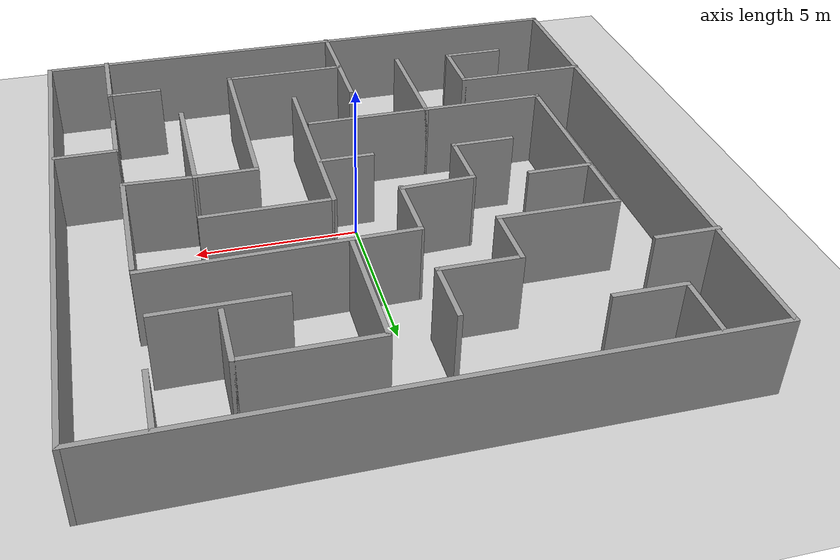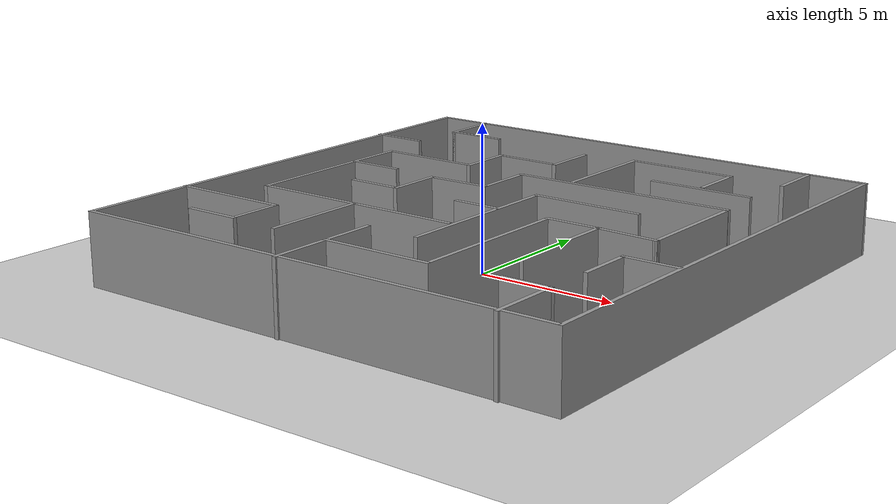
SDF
<sdf version="1.4">
 <world name="default">
  <light name="sun" type="directional">
   <pose>0 0 10 0 -0 0</pose>
   <diffuse>0.8 0.8 0.8 1</diffuse>
   <specular>0.1 0.1 0.1 1</specular>
   <attenuation>
    <range>1000</range>
    <constant>0.9</constant>
    <linear>0.01</linear>
    <quadratic>0.001</quadratic>
   </attenuation>
   <direction>-0.5 0.5 -1</direction>
  </light>
  <model name="ground_plane">
   <static>1</static>
   <link name="link">
    <collision name="collision">
     <geometry><plane><normal>0 0 1</normal><size>100 100</size></plane></geometry>
     <surface><friction><ode><mu>100</mu><mu2>50</mu2></ode></friction></surface>
    </collision>
    <visual name="visual">
     <cast_shadows>0</cast_shadows>
     <geometry><plane><normal>0 0 1</normal><size>100 100</size></plane></geometry>
     <material>
      <script><uri>file://media/materials/scripts/gazebo.material</uri><name>Gazebo/Grey</name></script>
     </material>
    </visual>
   </link>
  </model>
  <gravity>0 0 -9.8</gravity>
  <magnetic_field>6e-06 2.3e-05 -4.2e-05</magnetic_field>
  <atmosphere type="adiabatic"/>
  <physics name="default_physics" default="0" type="ode">
   <max_step_size>0.001</max_step_size>
   <real_time_factor>1</real_time_factor>
   <real_time_update_rate>1000</real_time_update_rate>
  </physics>
  <scene><ambient>0.4 0.4 0.4 1</ambient><background>0.7 0.7 0.7 1</background><shadows>1</shadows></scene>
  <spherical_coordinates>
   <surface_model>EARTH_WGS84</surface_model>
   <latitude_deg>0</latitude_deg>
   <longitude_deg>0</longitude_deg>
   <elevation>0</elevation>
   <heading_deg>0</heading_deg>
  </spherical_coordinates>
  <model name="myMaze_map">
   <link name="Wall_20">
    <pose>-0.135582 -8.3101 0 0 -0 0</pose>
    <visual name="Wall_20_Visual">
     <pose>0 0 1.25 0 -0 0</pose>
     <geometry><box><size>18 0.15 2.5</size></box></geometry>
     <material>
      <script><uri>file://media/materials/scripts/gazebo.material</uri><name>Gazebo/Grey</name></script>
      <ambient>1 1 1 1</ambient>
      <diffuse>0.7 0.7 0.7 1</diffuse>
      <specular>0.01 0.01 0.01 1</specular>
      <emissive>0 0 0 1</emissive>
     </material>
    </visual>
    <collision name="Wall_20_Collision">
     <pose>0 0 1.25 0 -0 0</pose>
     <geometry><box><size>18 0.15 2.5</size></box></geometry>
     <surface>
      <friction>
       <ode><mu>1</mu><mu2>1</mu2><fdir1>0 0 0</fdir1><slip1>0</slip1><slip2>0</slip2></ode>
       <torsional>
        <coefficient>1</coefficient>
        <patch_radius>0</patch_radius>
        <surface_radius>0</surface_radius>
        <use_patch_radius>1</use_patch_radius>
        <ode><slip>0</slip></ode>
       </torsional>
      </friction>
      <bounce><restitution_coefficient>0</restitution_coefficient><threshold>1e+06</threshold></bounce>
      <contact>
       <collide_without_contact>0</collide_without_contact>
       <collide_without_contact_bitmask>1</collide_without_contact_bitmask>
       <collide_bitmask>1</collide_bitmask>
       <ode>
        <soft_cfm>0</soft_cfm>
        <soft_erp>0.2</soft_erp>
        <kp>1e+13</kp>
        <kd>1</kd>
        <max_vel>0.01</max_vel>
        <min_depth>0</min_depth>
       </ode>
       <bullet>
        <split_impulse>1</split_impulse>
        <split_impulse_penetration_threshold>-0.01</split_impulse_penetration_threshold>
        <soft_cfm>0</soft_cfm>
        <soft_erp>0.2</soft_erp>
        <kp>1e+13</kp>
        <kd>1</kd>
       </bullet>
      </contact>
     </surface>
    </collision>
   </link>
   <link name="Wall_21">
    <pose>8.78942 0.614904 0 0 -0 1.5708</pose>
    <visual name="Wall_21_Visual">
     <pose>0 0 1.25 0 -0 0</pose>
     <geometry><box><size>18 0.15 2.5</size></box></geometry>
     <material>
      <script><uri>file://media/materials/scripts/gazebo.material</uri><name>Gazebo/Grey</name></script>
      <ambient>1 1 1 1</ambient>
      <diffuse>0.7 0.7 0.7 1</diffuse>
      <specular>0.01 0.01 0.01 1</specular>
      <emissive>0 0 0 1</emissive>
     </material>
    </visual>
    <collision name="Wall_21_Collision">
     <pose>0 0 1.25 0 -0 0</pose>
     <geometry><box><size>18 0.15 2.5</size></box></geometry>
     <surface>
      <friction>
       <ode><mu>1</mu><mu2>1</mu2><fdir1>0 0 0</fdir1><slip1>0</slip1><slip2>0</slip2></ode>
       <torsional>
        <coefficient>1</coefficient>
        <patch_radius>0</patch_radius>
        <surface_radius>0</surface_radius>
        <use_patch_radius>1</use_patch_radius>
        <ode><slip>0</slip></ode>
       </torsional>
      </friction>
      <bounce><restitution_coefficient>0</restitution_coefficient><threshold>1e+06</threshold></bounce>
      <contact>
       <collide_without_contact>0</collide_without_contact>
       <collide_without_contact_bitmask>1</collide_without_contact_bitmask>
       <collide_bitmask>1</collide_bitmask>
       <ode>
        <soft_cfm>0</soft_cfm>
        <soft_erp>0.2</soft_erp>
        <kp>1e+13</kp>
        <kd>1</kd>
        <max_vel>0.01</max_vel>
        <min_depth>0</min_depth>
       </ode>
       <bullet>
        <split_impulse>1</split_impulse>
        <split_impulse_penetration_threshold>-0.01</split_impulse_penetration_threshold>
        <soft_cfm>0</soft_cfm>
        <soft_erp>0.2</soft_erp>
        <kp>1e+13</kp>
        <kd>1</kd>
       </bullet>
      </contact>
     </surface>
    </collision>
   </link>
   <link name="Wall_22">
    <pose>-0.135582 9.5399 0 0 -0 3.14159</pose>
    <visual name="Wall_22_Visual">
     <pose>0 0 1.25 0 -0 0</pose>
     <geometry><box><size>18 0.15 2.5</size></box></geometry>
     <material>
      <script><uri>file://media/materials/scripts/gazebo.material</uri><name>Gazebo/Grey</name></script>
      <ambient>1 1 1 1</ambient>
      <diffuse>0.7 0.7 0.7 1</diffuse>
      <specular>0.01 0.01 0.01 1</specular>
      <emissive>0 0 0 1</emissive>
     </material>
    </visual>
    <collision name="Wall_22_Collision">
     <pose>0 0 1.25 0 -0 0</pose>
     <geometry><box><size>18 0.15 2.5</size></box></geometry>
     <surface>
      <friction>
       <ode><mu>1</mu><mu2>1</mu2><fdir1>0 0 0</fdir1><slip1>0</slip1><slip2>0</slip2></ode>
       <torsional>
        <coefficient>1</coefficient>
        <patch_radius>0</patch_radius>
        <surface_radius>0</surface_radius>
        <use_patch_radius>1</use_patch_radius>
        <ode><slip>0</slip></ode>
       </torsional>
      </friction>
      <bounce><restitution_coefficient>0</restitution_coefficient><threshold>1e+06</threshold></bounce>
      <contact>
       <collide_without_contact>0</collide_without_contact>
       <collide_without_contact_bitmask>1</collide_without_contact_bitmask>
       <collide_bitmask>1</collide_bitmask>
       <ode>
        <soft_cfm>0</soft_cfm>
        <soft_erp>0.2</soft_erp>
        <kp>1e+13</kp>
        <kd>1</kd>
        <max_vel>0.01</max_vel>
        <min_depth>0</min_depth>
       </ode>
       <bullet>
        <split_impulse>1</split_impulse>
        <split_impulse_penetration_threshold>-0.01</split_impulse_penetration_threshold>
        <soft_cfm>0</soft_cfm>
        <soft_erp>0.2</soft_erp>
        <kp>1e+13</kp>
        <kd>1</kd>
       </bullet>
      </contact>
     </surface>
    </collision>
   </link>
   <link name="Wall_23">
    <pose>-9.06058 0.614904 0 0 0 -1.5708</pose>
    <visual name="Wall_23_Visual">
     <pose>0 0 1.25 0 -0 0</pose>
     <geometry><box><size>18 0.15 2.5</size></box></geometry>
     <material>
      <script><uri>file://media/materials/scripts/gazebo.material</uri><name>Gazebo/Grey</name></script>
      <ambient>1 1 1 1</ambient>
      <diffuse>0.7 0.7 0.7 1</diffuse>
      <specular>0.01 0.01 0.01 1</specular>
      <emissive>0 0 0 1</emissive>
     </material>
    </visual>
    <collision name="Wall_23_Collision">
     <pose>0 0 1.25 0 -0 0</pose>
     <geometry><box><size>18 0.15 2.5</size></box></geometry>
     <surface>
      <friction>
       <ode><mu>1</mu><mu2>1</mu2><fdir1>0 0 0</fdir1><slip1>0</slip1><slip2>0</slip2></ode>
       <torsional>
        <coefficient>1</coefficient>
        <patch_radius>0</patch_radius>
        <surface_radius>0</surface_radius>
        <use_patch_radius>1</use_patch_radius>
        <ode><slip>0</slip></ode>
       </torsional>
      </friction>
      <bounce><restitution_coefficient>0</restitution_coefficient><threshold>1e+06</threshold></bounce>
      <contact>
       <collide_without_contact>0</collide_without_contact>
       <collide_without_contact_bitmask>1</collide_without_contact_bitmask>
       <collide_bitmask>1</collide_bitmask>
       <ode>
        <soft_cfm>0</soft_cfm>
        <soft_erp>0.2</soft_erp>
        <kp>1e+13</kp>
        <kd>1</kd>
        <max_vel>0.01</max_vel>
        <min_depth>0</min_depth>
       </ode>
       <bullet>
        <split_impulse>1</split_impulse>
        <split_impulse_penetration_threshold>-0.01</split_impulse_penetration_threshold>
        <soft_cfm>0</soft_cfm>
        <soft_erp>0.2</soft_erp>
        <kp>1e+13</kp>
        <kd>1</kd>
       </bullet>
      </contact>
     </surface>
    </collision>
   </link>
   <link name="Wall_25">
    <pose>-7.02908 -4.3298 0 0 -0 0</pose>
    <visual name="Wall_25_Visual">
     <pose>0 0 1.25 0 -0 0</pose>
     <geometry><box><size>4.25 0.15 2.5</size></box></geometry>
     <material>
      <script><uri>file://media/materials/scripts/gazebo.material</uri><name>Gazebo/Grey</name></script>
      <ambient>1 1 1 1</ambient>
      <diffuse>0.7 0.7 0.7 1</diffuse>
      <specular>0.01 0.01 0.01 1</specular>
      <emissive>0 0 0 1</emissive>
     </material>
    </visual>
    <collision name="Wall_25_Collision">
     <pose>0 0 1.25 0 -0 0</pose>
     <geometry><box><size>4.25 0.15 2.5</size></box></geometry>
     <surface>
      <friction>
       <ode><mu>1</mu><mu2>1</mu2><fdir1>0 0 0</fdir1><slip1>0</slip1><slip2>0</slip2></ode>
       <torsional>
        <coefficient>1</coefficient>
        <patch_radius>0</patch_radius>
        <surface_radius>0</surface_radius>
        <use_patch_radius>1</use_patch_radius>
        <ode><slip>0</slip></ode>
       </torsional>
      </friction>
      <bounce><restitution_coefficient>0</restitution_coefficient><threshold>1e+06</threshold></bounce>
      <contact>
       <collide_without_contact>0</collide_without_contact>
       <collide_without_contact_bitmask>1</collide_without_contact_bitmask>
       <collide_bitmask>1</collide_bitmask>
       <ode>
        <soft_cfm>0</soft_cfm>
        <soft_erp>0.2</soft_erp>
        <kp>1e+13</kp>
        <kd>1</kd>
        <max_vel>0.01</max_vel>
        <min_depth>0</min_depth>
       </ode>
       <bullet>
        <split_impulse>1</split_impulse>
        <split_impulse_penetration_threshold>-0.01</split_impulse_penetration_threshold>
        <soft_cfm>0</soft_cfm>
        <soft_erp>0.2</soft_erp>
        <kp>1e+13</kp>
        <kd>1</kd>
       </bullet>
      </contact>
     </surface>
    </collision>
   </link>
   <link name="Wall_26">
    <pose>-4.97908 -5.2548 0 0 0 -1.5708</pose>
    <visual name="Wall_26_Visual">
     <pose>0 0 1.25 0 -0 0</pose>
     <geometry><box><size>2 0.15 2.5</size></box></geometry>
     <material>
      <script><uri>file://media/materials/scripts/gazebo.material</uri><name>Gazebo/Grey</name></script>
      <ambient>1 1 1 1</ambient>
      <diffuse>0.7 0.7 0.7 1</diffuse>
      <specular>0.01 0.01 0.01 1</specular>
      <emissive>0 0 0 1</emissive>
     </material>
    </visual>
    <collision name="Wall_26_Collision">
     <pose>0 0 1.25 0 -0 0</pose>
     <geometry><box><size>2 0.15 2.5</size></box></geometry>
     <surface>
      <friction>
       <ode><mu>1</mu><mu2>1</mu2><fdir1>0 0 0</fdir1><slip1>0</slip1><slip2>0</slip2></ode>
       <torsional>
        <coefficient>1</coefficient>
        <patch_radius>0</patch_radius>
        <surface_radius>0</surface_radius>
        <use_patch_radius>1</use_patch_radius>
        <ode><slip>0</slip></ode>
       </torsional>
      </friction>
      <bounce><restitution_coefficient>0</restitution_coefficient><threshold>1e+06</threshold></bounce>
      <contact>
       <collide_without_contact>0</collide_without_contact>
       <collide_without_contact_bitmask>1</collide_without_contact_bitmask>
       <collide_bitmask>1</collide_bitmask>
       <ode>
        <soft_cfm>0</soft_cfm>
        <soft_erp>0.2</soft_erp>
        <kp>1e+13</kp>
        <kd>1</kd>
        <max_vel>0.01</max_vel>
        <min_depth>0</min_depth>
       </ode>
       <bullet>
        <split_impulse>1</split_impulse>
        <split_impulse_penetration_threshold>-0.01</split_impulse_penetration_threshold>
        <soft_cfm>0</soft_cfm>
        <soft_erp>0.2</soft_erp>
        <kp>1e+13</kp>
        <kd>1</kd>
       </bullet>
      </contact>
     </surface>
    </collision>
   </link>
   <link name="Wall_27">
    <pose>-5.90408 -6.1798 0 0 -0 3.14159</pose>
    <visual name="Wall_27_Visual">
     <pose>0 0 1.25 0 -0 0</pose>
     <geometry><box><size>2 0.15 2.5</size></box></geometry>
     <material>
      <script><uri>file://media/materials/scripts/gazebo.material</uri><name>Gazebo/Grey</name></script>
      <ambient>1 1 1 1</ambient>
      <diffuse>0.7 0.7 0.7 1</diffuse>
      <specular>0.01 0.01 0.01 1</specular>
      <emissive>0 0 0 1</emissive>
     </material>
    </visual>
    <collision name="Wall_27_Collision">
     <pose>0 0 1.25 0 -0 0</pose>
     <geometry><box><size>2 0.15 2.5</size></box></geometry>
     <surface>
      <friction>
       <ode><mu>1</mu><mu2>1</mu2><fdir1>0 0 0</fdir1><slip1>0</slip1><slip2>0</slip2></ode>
       <torsional>
        <coefficient>1</coefficient>
        <patch_radius>0</patch_radius>
        <surface_radius>0</surface_radius>
        <use_patch_radius>1</use_patch_radius>
        <ode><slip>0</slip></ode>
       </torsional>
      </friction>
      <bounce><restitution_coefficient>0</restitution_coefficient><threshold>1e+06</threshold></bounce>
      <contact>
       <collide_without_contact>0</collide_without_contact>
       <collide_without_contact_bitmask>1</collide_without_contact_bitmask>
       <collide_bitmask>1</collide_bitmask>
       <ode>
        <soft_cfm>0</soft_cfm>
        <soft_erp>0.2</soft_erp>
        <kp>1e+13</kp>
        <kd>1</kd>
        <max_vel>0.01</max_vel>
        <min_depth>0</min_depth>
       </ode>
       <bullet>
        <split_impulse>1</split_impulse>
        <split_impulse_penetration_threshold>-0.01</split_impulse_penetration_threshold>
        <soft_cfm>0</soft_cfm>
        <soft_erp>0.2</soft_erp>
        <kp>1e+13</kp>
        <kd>1</kd>
       </bullet>
      </contact>
     </surface>
    </collision>
   </link>
   <link name="Wall_29">
    <pose>-1.02842 -5.33571 0 0 0 -1.5708</pose>
    <visual name="Wall_29_Visual">
     <pose>0 0 1.25 0 -0 0</pose>
     <geometry><box><size>2 0.15 2.5</size></box></geometry>
     <material>
      <script><uri>file://media/materials/scripts/gazebo.material</uri><name>Gazebo/Grey</name></script>
      <ambient>1 1 1 1</ambient>
      <diffuse>0.7 0.7 0.7 1</diffuse>
      <specular>0.01 0.01 0.01 1</specular>
      <emissive>0 0 0 1</emissive>
     </material>
    </visual>
    <collision name="Wall_29_Collision">
     <pose>0 0 1.25 0 -0 0</pose>
     <geometry><box><size>2 0.15 2.5</size></box></geometry>
     <surface>
      <friction>
       <ode><mu>1</mu><mu2>1</mu2><fdir1>0 0 0</fdir1><slip1>0</slip1><slip2>0</slip2></ode>
       <torsional>
        <coefficient>1</coefficient>
        <patch_radius>0</patch_radius>
        <surface_radius>0</surface_radius>
        <use_patch_radius>1</use_patch_radius>
        <ode><slip>0</slip></ode>
       </torsional>
      </friction>
      <bounce><restitution_coefficient>0</restitution_coefficient><threshold>1e+06</threshold></bounce>
      <contact>
       <collide_without_contact>0</collide_without_contact>
       <collide_without_contact_bitmask>1</collide_without_contact_bitmask>
       <collide_bitmask>1</collide_bitmask>
       <ode>
        <soft_cfm>0</soft_cfm>
        <soft_erp>0.2</soft_erp>
        <kp>1e+13</kp>
        <kd>1</kd>
        <max_vel>0.01</max_vel>
        <min_depth>0</min_depth>
       </ode>
       <bullet>
        <split_impulse>1</split_impulse>
        <split_impulse_penetration_threshold>-0.01</split_impulse_penetration_threshold>
        <soft_cfm>0</soft_cfm>
        <soft_erp>0.2</soft_erp>
        <kp>1e+13</kp>
        <kd>1</kd>
       </bullet>
      </contact>
     </surface>
    </collision>
   </link>
   <link name="Wall_30">
    <pose>0.896581 -6.26071 0 0 -0 0</pose>
    <visual name="Wall_30_Visual">
     <pose>0 0 1.25 0 -0 0</pose>
     <geometry><box><size>4 0.15 2.5</size></box></geometry>
     <material>
      <script><uri>file://media/materials/scripts/gazebo.material</uri><name>Gazebo/Grey</name></script>
      <ambient>1 1 1 1</ambient>
      <diffuse>0.7 0.7 0.7 1</diffuse>
      <specular>0.01 0.01 0.01 1</specular>
      <emissive>0 0 0 1</emissive>
     </material>
    </visual>
    <collision name="Wall_30_Collision">
     <pose>0 0 1.25 0 -0 0</pose>
     <geometry><box><size>4 0.15 2.5</size></box></geometry>
     <surface>
      <friction>
       <ode><mu>1</mu><mu2>1</mu2><fdir1>0 0 0</fdir1><slip1>0</slip1><slip2>0</slip2></ode>
       <torsional>
        <coefficient>1</coefficient>
        <patch_radius>0</patch_radius>
        <surface_radius>0</surface_radius>
        <use_patch_radius>1</use_patch_radius>
        <ode><slip>0</slip></ode>
       </torsional>
      </friction>
      <bounce><restitution_coefficient>0</restitution_coefficient><threshold>1e+06</threshold></bounce>
      <contact>
       <collide_without_contact>0</collide_without_contact>
       <collide_without_contact_bitmask>1</collide_without_contact_bitmask>
       <collide_bitmask>1</collide_bitmask>
       <ode>
        <soft_cfm>0</soft_cfm>
        <soft_erp>0.2</soft_erp>
        <kp>1e+13</kp>
        <kd>1</kd>
        <max_vel>0.01</max_vel>
        <min_depth>0</min_depth>
       </ode>
       <bullet>
        <split_impulse>1</split_impulse>
        <split_impulse_penetration_threshold>-0.01</split_impulse_penetration_threshold>
        <soft_cfm>0</soft_cfm>
        <soft_erp>0.2</soft_erp>
        <kp>1e+13</kp>
        <kd>1</kd>
       </bullet>
      </contact>
     </surface>
    </collision>
   </link>
   <link name="Wall_31">
    <pose>2.82158 -3.33571 0 0 -0 1.5708</pose>
    <visual name="Wall_31_Visual">
     <pose>0 0 1.25 0 -0 0</pose>
     <geometry><box><size>6 0.15 2.5</size></box></geometry>
     <material>
      <script><uri>file://media/materials/scripts/gazebo.material</uri><name>Gazebo/Grey</name></script>
      <ambient>1 1 1 1</ambient>
      <diffuse>0.7 0.7 0.7 1</diffuse>
      <specular>0.01 0.01 0.01 1</specular>
      <emissive>0 0 0 1</emissive>
     </material>
    </visual>
    <collision name="Wall_31_Collision">
     <pose>0 0 1.25 0 -0 0</pose>
     <geometry><box><size>6 0.15 2.5</size></box></geometry>
     <surface>
      <friction>
       <ode><mu>1</mu><mu2>1</mu2><fdir1>0 0 0</fdir1><slip1>0</slip1><slip2>0</slip2></ode>
       <torsional>
        <coefficient>1</coefficient>
        <patch_radius>0</patch_radius>
        <surface_radius>0</surface_radius>
        <use_patch_radius>1</use_patch_radius>
        <ode><slip>0</slip></ode>
       </torsional>
      </friction>
      <bounce><restitution_coefficient>0</restitution_coefficient><threshold>1e+06</threshold></bounce>
      <contact>
       <collide_without_contact>0</collide_without_contact>
       <collide_without_contact_bitmask>1</collide_without_contact_bitmask>
       <collide_bitmask>1</collide_bitmask>
       <ode>
        <soft_cfm>0</soft_cfm>
        <soft_erp>0.2</soft_erp>
        <kp>1e+13</kp>
        <kd>1</kd>
        <max_vel>0.01</max_vel>
        <min_depth>0</min_depth>
       </ode>
       <bullet>
        <split_impulse>1</split_impulse>
        <split_impulse_penetration_threshold>-0.01</split_impulse_penetration_threshold>
        <soft_cfm>0</soft_cfm>
        <soft_erp>0.2</soft_erp>
        <kp>1e+13</kp>
        <kd>1</kd>
       </bullet>
      </contact>
     </surface>
    </collision>
   </link>
   <link name="Wall_32">
    <pose>3.74658 -0.410709 0 0 -0 0</pose>
    <visual name="Wall_32_Visual">
     <pose>0 0 1.25 0 -0 0</pose>
     <geometry><box><size>2 0.15 2.5</size></box></geometry>
     <material>
      <script><uri>file://media/materials/scripts/gazebo.material</uri><name>Gazebo/Grey</name></script>
      <ambient>1 1 1 1</ambient>
      <diffuse>0.7 0.7 0.7 1</diffuse>
      <specular>0.01 0.01 0.01 1</specular>
      <emissive>0 0 0 1</emissive>
     </material>
    </visual>
    <collision name="Wall_32_Collision">
     <pose>0 0 1.25 0 -0 0</pose>
     <geometry><box><size>2 0.15 2.5</size></box></geometry>
     <surface>
      <friction>
       <ode><mu>1</mu><mu2>1</mu2><fdir1>0 0 0</fdir1><slip1>0</slip1><slip2>0</slip2></ode>
       <torsional>
        <coefficient>1</coefficient>
        <patch_radius>0</patch_radius>
        <surface_radius>0</surface_radius>
        <use_patch_radius>1</use_patch_radius>
        <ode><slip>0</slip></ode>
       </torsional>
      </friction>
      <bounce><restitution_coefficient>0</restitution_coefficient><threshold>1e+06</threshold></bounce>
      <contact>
       <collide_without_contact>0</collide_without_contact>
       <collide_without_contact_bitmask>1</collide_without_contact_bitmask>
       <collide_bitmask>1</collide_bitmask>
       <ode>
        <soft_cfm>0</soft_cfm>
        <soft_erp>0.2</soft_erp>
        <kp>1e+13</kp>
        <kd>1</kd>
        <max_vel>0.01</max_vel>
        <min_depth>0</min_depth>
       </ode>
       <bullet>
        <split_impulse>1</split_impulse>
        <split_impulse_penetration_threshold>-0.01</split_impulse_penetration_threshold>
        <soft_cfm>0</soft_cfm>
        <soft_erp>0.2</soft_erp>
        <kp>1e+13</kp>
        <kd>1</kd>
       </bullet>
      </contact>
     </surface>
    </collision>
   </link>
   <link name="Wall_33">
    <pose>4.67158 -2.33571 0 0 0 -1.5708</pose>
    <visual name="Wall_33_Visual">
     <pose>0 0 1.25 0 -0 0</pose>
     <geometry><box><size>4 0.15 2.5</size></box></geometry>
     <material>
      <script><uri>file://media/materials/scripts/gazebo.material</uri><name>Gazebo/Grey</name></script>
      <ambient>1 1 1 1</ambient>
      <diffuse>0.7 0.7 0.7 1</diffuse>
      <specular>0.01 0.01 0.01 1</specular>
      <emissive>0 0 0 1</emissive>
     </material>
    </visual>
    <collision name="Wall_33_Collision">
     <pose>0 0 1.25 0 -0 0</pose>
     <geometry><box><size>4 0.15 2.5</size></box></geometry>
     <surface>
      <friction>
       <ode><mu>1</mu><mu2>1</mu2><fdir1>0 0 0</fdir1><slip1>0</slip1><slip2>0</slip2></ode>
       <torsional>
        <coefficient>1</coefficient>
        <patch_radius>0</patch_radius>
        <surface_radius>0</surface_radius>
        <use_patch_radius>1</use_patch_radius>
        <ode><slip>0</slip></ode>
       </torsional>
      </friction>
      <bounce><restitution_coefficient>0</restitution_coefficient><threshold>1e+06</threshold></bounce>
      <contact>
       <collide_without_contact>0</collide_without_contact>
       <collide_without_contact_bitmask>1</collide_without_contact_bitmask>
       <collide_bitmask>1</collide_bitmask>
       <ode>
        <soft_cfm>0</soft_cfm>
        <soft_erp>0.2</soft_erp>
        <kp>1e+13</kp>
        <kd>1</kd>
        <max_vel>0.01</max_vel>
        <min_depth>0</min_depth>
       </ode>
       <bullet>
        <split_impulse>1</split_impulse>
        <split_impulse_penetration_threshold>-0.01</split_impulse_penetration_threshold>
        <soft_cfm>0</soft_cfm>
        <soft_erp>0.2</soft_erp>
        <kp>1e+13</kp>
        <kd>1</kd>
       </bullet>
      </contact>
     </surface>
    </collision>
   </link>
   <link name="Wall_35">
    <pose>-1.02842 -7.31071 0 0 0 -1.5708</pose>
    <visual name="Wall_35_Visual">
     <pose>0 0 1.25 0 -0 0</pose>
     <geometry><box><size>2.25 0.15 2.5</size></box></geometry>
     <material>
      <script><uri>file://media/materials/scripts/gazebo.material</uri><name>Gazebo/Grey</name></script>
      <ambient>1 1 1 1</ambient>
      <diffuse>0.7 0.7 0.7 1</diffuse>
      <specular>0.01 0.01 0.01 1</specular>
      <emissive>0 0 0 1</emissive>
     </material>
    </visual>
    <collision name="Wall_35_Collision">
     <pose>0 0 1.25 0 -0 0</pose>
     <geometry><box><size>2.25 0.15 2.5</size></box></geometry>
     <surface>
      <friction>
       <ode><mu>1</mu><mu2>1</mu2><fdir1>0 0 0</fdir1><slip1>0</slip1><slip2>0</slip2></ode>
       <torsional>
        <coefficient>1</coefficient>
        <patch_radius>0</patch_radius>
        <surface_radius>0</surface_radius>
        <use_patch_radius>1</use_patch_radius>
        <ode><slip>0</slip></ode>
       </torsional>
      </friction>
      <bounce><restitution_coefficient>0</restitution_coefficient><threshold>1e+06</threshold></bounce>
      <contact>
       <collide_without_contact>0</collide_without_contact>
       <collide_without_contact_bitmask>1</collide_without_contact_bitmask>
       <collide_bitmask>1</collide_bitmask>
       <ode>
        <soft_cfm>0</soft_cfm>
        <soft_erp>0.2</soft_erp>
        <kp>1e+13</kp>
        <kd>1</kd>
        <max_vel>0.01</max_vel>
        <min_depth>0</min_depth>
       </ode>
       <bullet>
        <split_impulse>1</split_impulse>
        <split_impulse_penetration_threshold>-0.01</split_impulse_penetration_threshold>
        <soft_cfm>0</soft_cfm>
        <soft_erp>0.2</soft_erp>
        <kp>1e+13</kp>
        <kd>1</kd>
       </bullet>
      </contact>
     </surface>
    </collision>
   </link>
   <link name="Wall_37">
    <pose>6.86042 -7.20036 0 0 -0 1.5708</pose>
    <visual name="Wall_37_Visual">
     <pose>0 0 1.25 0 -0 0</pose>
     <geometry><box><size>2.5 0.15 2.5</size></box></geometry>
     <material>
      <script><uri>file://media/materials/scripts/gazebo.material</uri><name>Gazebo/Grey</name></script>
      <ambient>1 1 1 1</ambient>
      <diffuse>0.7 0.7 0.7 1</diffuse>
      <specular>0.01 0.01 0.01 1</specular>
      <emissive>0 0 0 1</emissive>
     </material>
    </visual>
    <collision name="Wall_37_Collision">
     <pose>0 0 1.25 0 -0 0</pose>
     <geometry><box><size>2.5 0.15 2.5</size></box></geometry>
     <surface>
      <friction>
       <ode><mu>1</mu><mu2>1</mu2><fdir1>0 0 0</fdir1><slip1>0</slip1><slip2>0</slip2></ode>
       <torsional>
        <coefficient>1</coefficient>
        <patch_radius>0</patch_radius>
        <surface_radius>0</surface_radius>
        <use_patch_radius>1</use_patch_radius>
        <ode><slip>0</slip></ode>
       </torsional>
      </friction>
      <bounce><restitution_coefficient>0</restitution_coefficient><threshold>1e+06</threshold></bounce>
      <contact>
       <collide_without_contact>0</collide_without_contact>
       <collide_without_contact_bitmask>1</collide_without_contact_bitmask>
       <collide_bitmask>1</collide_bitmask>
       <ode>
        <soft_cfm>0</soft_cfm>
        <soft_erp>0.2</soft_erp>
        <kp>1e+13</kp>
        <kd>1</kd>
        <max_vel>0.01</max_vel>
        <min_depth>0</min_depth>
       </ode>
       <bullet>
        <split_impulse>1</split_impulse>
        <split_impulse_penetration_threshold>-0.01</split_impulse_penetration_threshold>
        <soft_cfm>0</soft_cfm>
        <soft_erp>0.2</soft_erp>
        <kp>1e+13</kp>
        <kd>1</kd>
       </bullet>
      </contact>
     </surface>
    </collision>
   </link>
   <link name="Wall_38">
    <pose>6.06042 -6.02536 0 0 -0 3.14159</pose>
    <visual name="Wall_38_Visual">
     <pose>0 0 1.25 0 -0 0</pose>
     <geometry><box><size>1.75 0.15 2.5</size></box></geometry>
     <material>
      <script><uri>file://media/materials/scripts/gazebo.material</uri><name>Gazebo/Grey</name></script>
      <ambient>1 1 1 1</ambient>
      <diffuse>0.7 0.7 0.7 1</diffuse>
      <specular>0.01 0.01 0.01 1</specular>
      <emissive>0 0 0 1</emissive>
     </material>
    </visual>
    <collision name="Wall_38_Collision">
     <pose>0 0 1.25 0 -0 0</pose>
     <geometry><box><size>1.75 0.15 2.5</size></box></geometry>
     <surface>
      <friction>
       <ode><mu>1</mu><mu2>1</mu2><fdir1>0 0 0</fdir1><slip1>0</slip1><slip2>0</slip2></ode>
       <torsional>
        <coefficient>1</coefficient>
        <patch_radius>0</patch_radius>
        <surface_radius>0</surface_radius>
        <use_patch_radius>1</use_patch_radius>
        <ode><slip>0</slip></ode>
       </torsional>
      </friction>
      <bounce><restitution_coefficient>0</restitution_coefficient><threshold>1e+06</threshold></bounce>
      <contact>
       <collide_without_contact>0</collide_without_contact>
       <collide_without_contact_bitmask>1</collide_without_contact_bitmask>
       <collide_bitmask>1</collide_bitmask>
       <ode>
        <soft_cfm>0</soft_cfm>
        <soft_erp>0.2</soft_erp>
        <kp>1e+13</kp>
        <kd>1</kd>
        <max_vel>0.01</max_vel>
        <min_depth>0</min_depth>
       </ode>
       <bullet>
        <split_impulse>1</split_impulse>
        <split_impulse_penetration_threshold>-0.01</split_impulse_penetration_threshold>
        <soft_cfm>0</soft_cfm>
        <soft_erp>0.2</soft_erp>
        <kp>1e+13</kp>
        <kd>1</kd>
       </bullet>
      </contact>
     </surface>
    </collision>
   </link>
   <link name="Wall_40">
    <pose>6.86042 -3.36434 0 0 -0 1.5708</pose>
    <visual name="Wall_40_Visual">
     <pose>0 0 1.25 0 -0 0</pose>
     <geometry><box><size>2 0.15 2.5</size></box></geometry>
     <material>
      <script><uri>file://media/materials/scripts/gazebo.material</uri><name>Gazebo/Grey</name></script>
      <ambient>1 1 1 1</ambient>
      <diffuse>0.7 0.7 0.7 1</diffuse>
      <specular>0.01 0.01 0.01 1</specular>
      <emissive>0 0 0 1</emissive>
     </material>
    </visual>
    <collision name="Wall_40_Collision">
     <pose>0 0 1.25 0 -0 0</pose>
     <geometry><box><size>2 0.15 2.5</size></box></geometry>
     <surface>
      <friction>
       <ode><mu>1</mu><mu2>1</mu2><fdir1>0 0 0</fdir1><slip1>0</slip1><slip2>0</slip2></ode>
       <torsional>
        <coefficient>1</coefficient>
        <patch_radius>0</patch_radius>
        <surface_radius>0</surface_radius>
        <use_patch_radius>1</use_patch_radius>
        <ode><slip>0</slip></ode>
       </torsional>
      </friction>
      <bounce><restitution_coefficient>0</restitution_coefficient><threshold>1e+06</threshold></bounce>
      <contact>
       <collide_without_contact>0</collide_without_contact>
       <collide_without_contact_bitmask>1</collide_without_contact_bitmask>
       <collide_bitmask>1</collide_bitmask>
       <ode>
        <soft_cfm>0</soft_cfm>
        <soft_erp>0.2</soft_erp>
        <kp>1e+13</kp>
        <kd>1</kd>
        <max_vel>0.01</max_vel>
        <min_depth>0</min_depth>
       </ode>
       <bullet>
        <split_impulse>1</split_impulse>
        <split_impulse_penetration_threshold>-0.01</split_impulse_penetration_threshold>
        <soft_cfm>0</soft_cfm>
        <soft_erp>0.2</soft_erp>
        <kp>1e+13</kp>
        <kd>1</kd>
       </bullet>
      </contact>
     </surface>
    </collision>
   </link>
   <link name="Wall_41">
    <pose>7.78542 -2.43934 0 0 -0 0</pose>
    <visual name="Wall_41_Visual">
     <pose>0 0 1.25 0 -0 0</pose>
     <geometry><box><size>2 0.15 2.5</size></box></geometry>
     <material>
      <script><uri>file://media/materials/scripts/gazebo.material</uri><name>Gazebo/Grey</name></script>
      <ambient>1 1 1 1</ambient>
      <diffuse>0.7 0.7 0.7 1</diffuse>
      <specular>0.01 0.01 0.01 1</specular>
      <emissive>0 0 0 1</emissive>
     </material>
    </visual>
    <collision name="Wall_41_Collision">
     <pose>0 0 1.25 0 -0 0</pose>
     <geometry><box><size>2 0.15 2.5</size></box></geometry>
     <surface>
      <friction>
       <ode><mu>1</mu><mu2>1</mu2><fdir1>0 0 0</fdir1><slip1>0</slip1><slip2>0</slip2></ode>
       <torsional>
        <coefficient>1</coefficient>
        <patch_radius>0</patch_radius>
        <surface_radius>0</surface_radius>
        <use_patch_radius>1</use_patch_radius>
        <ode><slip>0</slip></ode>
       </torsional>
      </friction>
      <bounce><restitution_coefficient>0</restitution_coefficient><threshold>1e+06</threshold></bounce>
      <contact>
       <collide_without_contact>0</collide_without_contact>
       <collide_without_contact_bitmask>1</collide_without_contact_bitmask>
       <collide_bitmask>1</collide_bitmask>
       <ode>
        <soft_cfm>0</soft_cfm>
        <soft_erp>0.2</soft_erp>
        <kp>1e+13</kp>
        <kd>1</kd>
        <max_vel>0.01</max_vel>
        <min_depth>0</min_depth>
       </ode>
       <bullet>
        <split_impulse>1</split_impulse>
        <split_impulse_penetration_threshold>-0.01</split_impulse_penetration_threshold>
        <soft_cfm>0</soft_cfm>
        <soft_erp>0.2</soft_erp>
        <kp>1e+13</kp>
        <kd>1</kd>
       </bullet>
      </contact>
     </surface>
    </collision>
   </link>
   <link name="Wall_43">
    <pose>-3.13211 -4.47166 0 0 -0 1.5708</pose>
    <visual name="Wall_43_Visual">
     <pose>0 0 1.25 0 -0 0</pose>
     <geometry><box><size>3.75 0.15 2.5</size></box></geometry>
     <material>
      <script><uri>file://media/materials/scripts/gazebo.material</uri><name>Gazebo/Grey</name></script>
      <ambient>1 1 1 1</ambient>
      <diffuse>0.7 0.7 0.7 1</diffuse>
      <specular>0.01 0.01 0.01 1</specular>
      <emissive>0 0 0 1</emissive>
     </material>
    </visual>
    <collision name="Wall_43_Collision">
     <pose>0 0 1.25 0 -0 0</pose>
     <geometry><box><size>3.75 0.15 2.5</size></box></geometry>
     <surface>
      <friction>
       <ode><mu>1</mu><mu2>1</mu2><fdir1>0 0 0</fdir1><slip1>0</slip1><slip2>0</slip2></ode>
       <torsional>
        <coefficient>1</coefficient>
        <patch_radius>0</patch_radius>
        <surface_radius>0</surface_radius>
        <use_patch_radius>1</use_patch_radius>
        <ode><slip>0</slip></ode>
       </torsional>
      </friction>
      <bounce><restitution_coefficient>0</restitution_coefficient><threshold>1e+06</threshold></bounce>
      <contact>
       <collide_without_contact>0</collide_without_contact>
       <collide_without_contact_bitmask>1</collide_without_contact_bitmask>
       <collide_bitmask>1</collide_bitmask>
       <ode>
        <soft_cfm>0</soft_cfm>
        <soft_erp>0.2</soft_erp>
        <kp>1e+13</kp>
        <kd>1</kd>
        <max_vel>0.01</max_vel>
        <min_depth>0</min_depth>
       </ode>
       <bullet>
        <split_impulse>1</split_impulse>
        <split_impulse_penetration_threshold>-0.01</split_impulse_penetration_threshold>
        <soft_cfm>0</soft_cfm>
        <soft_erp>0.2</soft_erp>
        <kp>1e+13</kp>
        <kd>1</kd>
       </bullet>
      </contact>
     </surface>
    </collision>
   </link>
   <link name="Wall_44">
    <pose>-5.05711 -2.67166 0 0 -0 3.14159</pose>
    <visual name="Wall_44_Visual">
     <pose>0 0 1.25 0 -0 0</pose>
     <geometry><box><size>4 0.15 2.5</size></box></geometry>
     <material>
      <script><uri>file://media/materials/scripts/gazebo.material</uri><name>Gazebo/Grey</name></script>
      <ambient>1 1 1 1</ambient>
      <diffuse>0.7 0.7 0.7 1</diffuse>
      <specular>0.01 0.01 0.01 1</specular>
      <emissive>0 0 0 1</emissive>
     </material>
    </visual>
    <collision name="Wall_44_Collision">
     <pose>0 0 1.25 0 -0 0</pose>
     <geometry><box><size>4 0.15 2.5</size></box></geometry>
     <surface>
      <friction>
       <ode><mu>1</mu><mu2>1</mu2><fdir1>0 0 0</fdir1><slip1>0</slip1><slip2>0</slip2></ode>
       <torsional>
        <coefficient>1</coefficient>
        <patch_radius>0</patch_radius>
        <surface_radius>0</surface_radius>
        <use_patch_radius>1</use_patch_radius>
        <ode><slip>0</slip></ode>
       </torsional>
      </friction>
      <bounce><restitution_coefficient>0</restitution_coefficient><threshold>1e+06</threshold></bounce>
      <contact>
       <collide_without_contact>0</collide_without_contact>
       <collide_without_contact_bitmask>1</collide_without_contact_bitmask>
       <collide_bitmask>1</collide_bitmask>
       <ode>
        <soft_cfm>0</soft_cfm>
        <soft_erp>0.2</soft_erp>
        <kp>1e+13</kp>
        <kd>1</kd>
        <max_vel>0.01</max_vel>
        <min_depth>0</min_depth>
       </ode>
       <bullet>
        <split_impulse>1</split_impulse>
        <split_impulse_penetration_threshold>-0.01</split_impulse_penetration_threshold>
        <soft_cfm>0</soft_cfm>
        <soft_erp>0.2</soft_erp>
        <kp>1e+13</kp>
        <kd>1</kd>
       </bullet>
      </contact>
     </surface>
    </collision>
   </link>
   <link name="Wall_45">
    <pose>-6.98211 0.503335 0 0 -0 1.5708</pose>
    <visual name="Wall_45_Visual">
     <pose>0 0 1.25 0 -0 0</pose>
     <geometry><box><size>6.5 0.15 2.5</size></box></geometry>
     <material>
      <script><uri>file://media/materials/scripts/gazebo.material</uri><name>Gazebo/Grey</name></script>
      <ambient>1 1 1 1</ambient>
      <diffuse>0.7 0.7 0.7 1</diffuse>
      <specular>0.01 0.01 0.01 1</specular>
      <emissive>0 0 0 1</emissive>
     </material>
    </visual>
    <collision name="Wall_45_Collision">
     <pose>0 0 1.25 0 -0 0</pose>
     <geometry><box><size>6.5 0.15 2.5</size></box></geometry>
     <surface>
      <friction>
       <ode><mu>1</mu><mu2>1</mu2><fdir1>0 0 0</fdir1><slip1>0</slip1><slip2>0</slip2></ode>
       <torsional>
        <coefficient>1</coefficient>
        <patch_radius>0</patch_radius>
        <surface_radius>0</surface_radius>
        <use_patch_radius>1</use_patch_radius>
        <ode><slip>0</slip></ode>
       </torsional>
      </friction>
      <bounce><restitution_coefficient>0</restitution_coefficient><threshold>1e+06</threshold></bounce>
      <contact>
       <collide_without_contact>0</collide_without_contact>
       <collide_without_contact_bitmask>1</collide_without_contact_bitmask>
       <collide_bitmask>1</collide_bitmask>
       <ode>
        <soft_cfm>0</soft_cfm>
        <soft_erp>0.2</soft_erp>
        <kp>1e+13</kp>
        <kd>1</kd>
        <max_vel>0.01</max_vel>
        <min_depth>0</min_depth>
       </ode>
       <bullet>
        <split_impulse>1</split_impulse>
        <split_impulse_penetration_threshold>-0.01</split_impulse_penetration_threshold>
        <soft_cfm>0</soft_cfm>
        <soft_erp>0.2</soft_erp>
        <kp>1e+13</kp>
        <kd>1</kd>
       </bullet>
      </contact>
     </surface>
    </collision>
   </link>
   <link name="Wall_46">
    <pose>-5.18211 3.67834 0 0 -0 0</pose>
    <visual name="Wall_46_Visual">
     <pose>0 0 1.25 0 -0 0</pose>
     <geometry><box><size>3.75 0.15 2.5</size></box></geometry>
     <material>
      <script><uri>file://media/materials/scripts/gazebo.material</uri><name>Gazebo/Grey</name></script>
      <ambient>1 1 1 1</ambient>
      <diffuse>0.7 0.7 0.7 1</diffuse>
      <specular>0.01 0.01 0.01 1</specular>
      <emissive>0 0 0 1</emissive>
     </material>
    </visual>
    <collision name="Wall_46_Collision">
     <pose>0 0 1.25 0 -0 0</pose>
     <geometry><box><size>3.75 0.15 2.5</size></box></geometry>
     <surface>
      <friction>
       <ode><mu>1</mu><mu2>1</mu2><fdir1>0 0 0</fdir1><slip1>0</slip1><slip2>0</slip2></ode>
       <torsional>
        <coefficient>1</coefficient>
        <patch_radius>0</patch_radius>
        <surface_radius>0</surface_radius>
        <use_patch_radius>1</use_patch_radius>
        <ode><slip>0</slip></ode>
       </torsional>
      </friction>
      <bounce><restitution_coefficient>0</restitution_coefficient><threshold>1e+06</threshold></bounce>
      <contact>
       <collide_without_contact>0</collide_without_contact>
       <collide_without_contact_bitmask>1</collide_without_contact_bitmask>
       <collide_bitmask>1</collide_bitmask>
       <ode>
        <soft_cfm>0</soft_cfm>
        <soft_erp>0.2</soft_erp>
        <kp>1e+13</kp>
        <kd>1</kd>
        <max_vel>0.01</max_vel>
        <min_depth>0</min_depth>
       </ode>
       <bullet>
        <split_impulse>1</split_impulse>
        <split_impulse_penetration_threshold>-0.01</split_impulse_penetration_threshold>
        <soft_cfm>0</soft_cfm>
        <soft_erp>0.2</soft_erp>
        <kp>1e+13</kp>
        <kd>1</kd>
       </bullet>
      </contact>
     </surface>
    </collision>
   </link>
   <link name="Wall_47">
    <pose>-3.38211 4.60333 0 0 -0 1.5708</pose>
    <visual name="Wall_47_Visual">
     <pose>0 0 1.25 0 -0 0</pose>
     <geometry><box><size>2 0.15 2.5</size></box></geometry>
     <material>
      <script><uri>file://media/materials/scripts/gazebo.material</uri><name>Gazebo/Grey</name></script>
      <ambient>1 1 1 1</ambient>
      <diffuse>0.7 0.7 0.7 1</diffuse>
      <specular>0.01 0.01 0.01 1</specular>
      <emissive>0 0 0 1</emissive>
     </material>
    </visual>
    <collision name="Wall_47_Collision">
     <pose>0 0 1.25 0 -0 0</pose>
     <geometry><box><size>2 0.15 2.5</size></box></geometry>
     <surface>
      <friction>
       <ode><mu>1</mu><mu2>1</mu2><fdir1>0 0 0</fdir1><slip1>0</slip1><slip2>0</slip2></ode>
       <torsional>
        <coefficient>1</coefficient>
        <patch_radius>0</patch_radius>
        <surface_radius>0</surface_radius>
        <use_patch_radius>1</use_patch_radius>
        <ode><slip>0</slip></ode>
       </torsional>
      </friction>
      <bounce><restitution_coefficient>0</restitution_coefficient><threshold>1e+06</threshold></bounce>
      <contact>
       <collide_without_contact>0</collide_without_contact>
       <collide_without_contact_bitmask>1</collide_without_contact_bitmask>
       <collide_bitmask>1</collide_bitmask>
       <ode>
        <soft_cfm>0</soft_cfm>
        <soft_erp>0.2</soft_erp>
        <kp>1e+13</kp>
        <kd>1</kd>
        <max_vel>0.01</max_vel>
        <min_depth>0</min_depth>
       </ode>
       <bullet>
        <split_impulse>1</split_impulse>
        <split_impulse_penetration_threshold>-0.01</split_impulse_penetration_threshold>
        <soft_cfm>0</soft_cfm>
        <soft_erp>0.2</soft_erp>
        <kp>1e+13</kp>
        <kd>1</kd>
       </bullet>
      </contact>
     </surface>
    </collision>
   </link>
   <link name="Wall_48">
    <pose>-2.20711 5.52834 0 0 -0 0</pose>
    <visual name="Wall_48_Visual">
     <pose>0 0 1.25 0 -0 0</pose>
     <geometry><box><size>2.5 0.15 2.5</size></box></geometry>
     <material>
      <script><uri>file://media/materials/scripts/gazebo.material</uri><name>Gazebo/Grey</name></script>
      <ambient>1 1 1 1</ambient>
      <diffuse>0.7 0.7 0.7 1</diffuse>
      <specular>0.01 0.01 0.01 1</specular>
      <emissive>0 0 0 1</emissive>
     </material>
    </visual>
    <collision name="Wall_48_Collision">
     <pose>0 0 1.25 0 -0 0</pose>
     <geometry><box><size>2.5 0.15 2.5</size></box></geometry>
     <surface>
      <friction>
       <ode><mu>1</mu><mu2>1</mu2><fdir1>0 0 0</fdir1><slip1>0</slip1><slip2>0</slip2></ode>
       <torsional>
        <coefficient>1</coefficient>
        <patch_radius>0</patch_radius>
        <surface_radius>0</surface_radius>
        <use_patch_radius>1</use_patch_radius>
        <ode><slip>0</slip></ode>
       </torsional>
      </friction>
      <bounce><restitution_coefficient>0</restitution_coefficient><threshold>1e+06</threshold></bounce>
      <contact>
       <collide_without_contact>0</collide_without_contact>
       <collide_without_contact_bitmask>1</collide_without_contact_bitmask>
       <collide_bitmask>1</collide_bitmask>
       <ode>
        <soft_cfm>0</soft_cfm>
        <soft_erp>0.2</soft_erp>
        <kp>1e+13</kp>
        <kd>1</kd>
        <max_vel>0.01</max_vel>
        <min_depth>0</min_depth>
       </ode>
       <bullet>
        <split_impulse>1</split_impulse>
        <split_impulse_penetration_threshold>-0.01</split_impulse_penetration_threshold>
        <soft_cfm>0</soft_cfm>
        <soft_erp>0.2</soft_erp>
        <kp>1e+13</kp>
        <kd>1</kd>
       </bullet>
      </contact>
     </surface>
    </collision>
   </link>
   <link name="Wall_49">
    <pose>-1.03211 6.45334 0 0 -0 1.5708</pose>
    <visual name="Wall_49_Visual">
     <pose>0 0 1.25 0 -0 0</pose>
     <geometry><box><size>2 0.15 2.5</size></box></geometry>
     <material>
      <script><uri>file://media/materials/scripts/gazebo.material</uri><name>Gazebo/Grey</name></script>
      <ambient>1 1 1 1</ambient>
      <diffuse>0.7 0.7 0.7 1</diffuse>
      <specular>0.01 0.01 0.01 1</specular>
      <emissive>0 0 0 1</emissive>
     </material>
    </visual>
    <collision name="Wall_49_Collision">
     <pose>0 0 1.25 0 -0 0</pose>
     <geometry><box><size>2 0.15 2.5</size></box></geometry>
     <surface>
      <friction>
       <ode><mu>1</mu><mu2>1</mu2><fdir1>0 0 0</fdir1><slip1>0</slip1><slip2>0</slip2></ode>
       <torsional>
        <coefficient>1</coefficient>
        <patch_radius>0</patch_radius>
        <surface_radius>0</surface_radius>
        <use_patch_radius>1</use_patch_radius>
        <ode><slip>0</slip></ode>
       </torsional>
      </friction>
      <bounce><restitution_coefficient>0</restitution_coefficient><threshold>1e+06</threshold></bounce>
      <contact>
       <collide_without_contact>0</collide_without_contact>
       <collide_without_contact_bitmask>1</collide_without_contact_bitmask>
       <collide_bitmask>1</collide_bitmask>
       <ode>
        <soft_cfm>0</soft_cfm>
        <soft_erp>0.2</soft_erp>
        <kp>1e+13</kp>
        <kd>1</kd>
        <max_vel>0.01</max_vel>
        <min_depth>0</min_depth>
       </ode>
       <bullet>
        <split_impulse>1</split_impulse>
        <split_impulse_penetration_threshold>-0.01</split_impulse_penetration_threshold>
        <soft_cfm>0</soft_cfm>
        <soft_erp>0.2</soft_erp>
        <kp>1e+13</kp>
        <kd>1</kd>
       </bullet>
      </contact>
     </surface>
    </collision>
   </link>
   <link name="Wall_51">
    <pose>-6.00993 1.69808 0 0 -0 0</pose>
    <visual name="Wall_51_Visual">
     <pose>0 0 1.25 0 -0 0</pose>
     <geometry><box><size>2 0.15 2.5</size></box></geometry>
     <material>
      <script><uri>file://media/materials/scripts/gazebo.material</uri><name>Gazebo/Grey</name></script>
      <ambient>1 1 1 1</ambient>
      <diffuse>0.7 0.7 0.7 1</diffuse>
      <specular>0.01 0.01 0.01 1</specular>
      <emissive>0 0 0 1</emissive>
     </material>
    </visual>
    <collision name="Wall_51_Collision">
     <pose>0 0 1.25 0 -0 0</pose>
     <geometry><box><size>2 0.15 2.5</size></box></geometry>
     <surface>
      <friction>
       <ode><mu>1</mu><mu2>1</mu2><fdir1>0 0 0</fdir1><slip1>0</slip1><slip2>0</slip2></ode>
       <torsional>
        <coefficient>1</coefficient>
        <patch_radius>0</patch_radius>
        <surface_radius>0</surface_radius>
        <use_patch_radius>1</use_patch_radius>
        <ode><slip>0</slip></ode>
       </torsional>
      </friction>
      <bounce><restitution_coefficient>0</restitution_coefficient><threshold>1e+06</threshold></bounce>
      <contact>
       <collide_without_contact>0</collide_without_contact>
       <collide_without_contact_bitmask>1</collide_without_contact_bitmask>
       <collide_bitmask>1</collide_bitmask>
       <ode>
        <soft_cfm>0</soft_cfm>
        <soft_erp>0.2</soft_erp>
        <kp>1e+13</kp>
        <kd>1</kd>
        <max_vel>0.01</max_vel>
        <min_depth>0</min_depth>
       </ode>
       <bullet>
        <split_impulse>1</split_impulse>
        <split_impulse_penetration_threshold>-0.01</split_impulse_penetration_threshold>
        <soft_cfm>0</soft_cfm>
        <soft_erp>0.2</soft_erp>
        <kp>1e+13</kp>
        <kd>1</kd>
       </bullet>
      </contact>
     </surface>
    </collision>
   </link>
   <link name="Wall_53">
    <pose>-4.27034 -0.324696 0 0 -0 0</pose>
    <visual name="Wall_53_Visual">
     <pose>0 0 1.25 0 -0 0</pose>
     <geometry><box><size>2 0.15 2.5</size></box></geometry>
     <material>
      <script><uri>file://media/materials/scripts/gazebo.material</uri><name>Gazebo/Grey</name></script>
      <ambient>1 1 1 1</ambient>
      <diffuse>0.7 0.7 0.7 1</diffuse>
      <specular>0.01 0.01 0.01 1</specular>
      <emissive>0 0 0 1</emissive>
     </material>
    </visual>
    <collision name="Wall_53_Collision">
     <pose>0 0 1.25 0 -0 0</pose>
     <geometry><box><size>2 0.15 2.5</size></box></geometry>
     <surface>
      <friction>
       <ode><mu>1</mu><mu2>1</mu2><fdir1>0 0 0</fdir1><slip1>0</slip1><slip2>0</slip2></ode>
       <torsional>
        <coefficient>1</coefficient>
        <patch_radius>0</patch_radius>
        <surface_radius>0</surface_radius>
        <use_patch_radius>1</use_patch_radius>
        <ode><slip>0</slip></ode>
       </torsional>
      </friction>
      <bounce><restitution_coefficient>0</restitution_coefficient><threshold>1e+06</threshold></bounce>
      <contact>
       <collide_without_contact>0</collide_without_contact>
       <collide_without_contact_bitmask>1</collide_without_contact_bitmask>
       <collide_bitmask>1</collide_bitmask>
       <ode>
        <soft_cfm>0</soft_cfm>
        <soft_erp>0.2</soft_erp>
        <kp>1e+13</kp>
        <kd>1</kd>
        <max_vel>0.01</max_vel>
        <min_depth>0</min_depth>
       </ode>
       <bullet>
        <split_impulse>1</split_impulse>
        <split_impulse_penetration_threshold>-0.01</split_impulse_penetration_threshold>
        <soft_cfm>0</soft_cfm>
        <soft_erp>0.2</soft_erp>
        <kp>1e+13</kp>
        <kd>1</kd>
       </bullet>
      </contact>
     </surface>
    </collision>
   </link>
   <link name="Wall_54">
    <pose>-3.34534 0.600304 0 0 -0 1.5708</pose>
    <visual name="Wall_54_Visual">
     <pose>0 0 1.25 0 -0 0</pose>
     <geometry><box><size>2 0.15 2.5</size></box></geometry>
     <material>
      <script><uri>file://media/materials/scripts/gazebo.material</uri><name>Gazebo/Grey</name></script>
      <ambient>1 1 1 1</ambient>
      <diffuse>0.7 0.7 0.7 1</diffuse>
      <specular>0.01 0.01 0.01 1</specular>
      <emissive>0 0 0 1</emissive>
     </material>
    </visual>
    <collision name="Wall_54_Collision">
     <pose>0 0 1.25 0 -0 0</pose>
     <geometry><box><size>2 0.15 2.5</size></box></geometry>
     <surface>
      <friction>
       <ode><mu>1</mu><mu2>1</mu2><fdir1>0 0 0</fdir1><slip1>0</slip1><slip2>0</slip2></ode>
       <torsional>
        <coefficient>1</coefficient>
        <patch_radius>0</patch_radius>
        <surface_radius>0</surface_radius>
        <use_patch_radius>1</use_patch_radius>
        <ode><slip>0</slip></ode>
       </torsional>
      </friction>
      <bounce><restitution_coefficient>0</restitution_coefficient><threshold>1e+06</threshold></bounce>
      <contact>
       <collide_without_contact>0</collide_without_contact>
       <collide_without_contact_bitmask>1</collide_without_contact_bitmask>
       <collide_bitmask>1</collide_bitmask>
       <ode>
        <soft_cfm>0</soft_cfm>
        <soft_erp>0.2</soft_erp>
        <kp>1e+13</kp>
        <kd>1</kd>
        <max_vel>0.01</max_vel>
        <min_depth>0</min_depth>
       </ode>
       <bullet>
        <split_impulse>1</split_impulse>
        <split_impulse_penetration_threshold>-0.01</split_impulse_penetration_threshold>
        <soft_cfm>0</soft_cfm>
        <soft_erp>0.2</soft_erp>
        <kp>1e+13</kp>
        <kd>1</kd>
       </bullet>
      </contact>
     </surface>
    </collision>
   </link>
   <link name="Wall_55">
    <pose>-2.25489 1.56576 0 0 -0 0.037083</pose>
    <visual name="Wall_55_Visual">
     <pose>0 0 1.25 0 -0 0</pose>
     <geometry><box><size>2.33241 0.15 2.5</size></box></geometry>
     <material>
      <script><uri>file://media/materials/scripts/gazebo.material</uri><name>Gazebo/Grey</name></script>
      <ambient>1 1 1 1</ambient>
      <diffuse>0.7 0.7 0.7 1</diffuse>
      <specular>0.01 0.01 0.01 1</specular>
      <emissive>0 0 0 1</emissive>
     </material>
    </visual>
    <collision name="Wall_55_Collision">
     <pose>0 0 1.25 0 -0 0</pose>
     <geometry><box><size>2.33241 0.15 2.5</size></box></geometry>
     <surface>
      <friction>
       <ode><mu>1</mu><mu2>1</mu2><fdir1>0 0 0</fdir1><slip1>0</slip1><slip2>0</slip2></ode>
       <torsional>
        <coefficient>1</coefficient>
        <patch_radius>0</patch_radius>
        <surface_radius>0</surface_radius>
        <use_patch_radius>1</use_patch_radius>
        <ode><slip>0</slip></ode>
       </torsional>
      </friction>
      <bounce><restitution_coefficient>0</restitution_coefficient><threshold>1e+06</threshold></bounce>
      <contact>
       <collide_without_contact>0</collide_without_contact>
       <collide_without_contact_bitmask>1</collide_without_contact_bitmask>
       <collide_bitmask>1</collide_bitmask>
       <ode>
        <soft_cfm>0</soft_cfm>
        <soft_erp>0.2</soft_erp>
        <kp>1e+13</kp>
        <kd>1</kd>
        <max_vel>0.01</max_vel>
        <min_depth>0</min_depth>
       </ode>
       <bullet>
        <split_impulse>1</split_impulse>
        <split_impulse_penetration_threshold>-0.01</split_impulse_penetration_threshold>
        <soft_cfm>0</soft_cfm>
        <soft_erp>0.2</soft_erp>
        <kp>1e+13</kp>
        <kd>1</kd>
       </bullet>
      </contact>
     </surface>
    </collision>
   </link>
   <link name="Wall_56">
    <pose>-1.12398 2.61576 0 0 -0 1.5708</pose>
    <visual name="Wall_56_Visual">
     <pose>0 0 1.25 0 -0 0</pose>
     <geometry><box><size>2.25 0.15 2.5</size></box></geometry>
     <material>
      <script><uri>file://media/materials/scripts/gazebo.material</uri><name>Gazebo/Grey</name></script>
      <ambient>1 1 1 1</ambient>
      <diffuse>0.7 0.7 0.7 1</diffuse>
      <specular>0.01 0.01 0.01 1</specular>
      <emissive>0 0 0 1</emissive>
     </material>
    </visual>
    <collision name="Wall_56_Collision">
     <pose>0 0 1.25 0 -0 0</pose>
     <geometry><box><size>2.25 0.15 2.5</size></box></geometry>
     <surface>
      <friction>
       <ode><mu>1</mu><mu2>1</mu2><fdir1>0 0 0</fdir1><slip1>0</slip1><slip2>0</slip2></ode>
       <torsional>
        <coefficient>1</coefficient>
        <patch_radius>0</patch_radius>
        <surface_radius>0</surface_radius>
        <use_patch_radius>1</use_patch_radius>
        <ode><slip>0</slip></ode>
       </torsional>
      </friction>
      <bounce><restitution_coefficient>0</restitution_coefficient><threshold>1e+06</threshold></bounce>
      <contact>
       <collide_without_contact>0</collide_without_contact>
       <collide_without_contact_bitmask>1</collide_without_contact_bitmask>
       <collide_bitmask>1</collide_bitmask>
       <ode>
        <soft_cfm>0</soft_cfm>
        <soft_erp>0.2</soft_erp>
        <kp>1e+13</kp>
        <kd>1</kd>
        <max_vel>0.01</max_vel>
        <min_depth>0</min_depth>
       </ode>
       <bullet>
        <split_impulse>1</split_impulse>
        <split_impulse_penetration_threshold>-0.01</split_impulse_penetration_threshold>
        <soft_cfm>0</soft_cfm>
        <soft_erp>0.2</soft_erp>
        <kp>1e+13</kp>
        <kd>1</kd>
       </bullet>
      </contact>
     </surface>
    </collision>
   </link>
   <link name="Wall_57">
    <pose>2.82125 3.72644 0 0 -0 0.01538</pose>
    <visual name="Wall_57_Visual">
     <pose>0 0 1.25 0 -0 0</pose>
     <geometry><box><size>8.04139 0.15 2.5</size></box></geometry>
     <material>
      <script><uri>file://media/materials/scripts/gazebo.material</uri><name>Gazebo/Grey</name></script>
      <ambient>1 1 1 1</ambient>
      <diffuse>0.7 0.7 0.7 1</diffuse>
      <specular>0.01 0.01 0.01 1</specular>
      <emissive>0 0 0 1</emissive>
     </material>
    </visual>
    <collision name="Wall_57_Collision">
     <pose>0 0 1.25 0 -0 0</pose>
     <geometry><box><size>8.04139 0.15 2.5</size></box></geometry>
     <surface>
      <friction>
       <ode><mu>1</mu><mu2>1</mu2><fdir1>0 0 0</fdir1><slip1>0</slip1><slip2>0</slip2></ode>
       <torsional>
        <coefficient>1</coefficient>
        <patch_radius>0</patch_radius>
        <surface_radius>0</surface_radius>
        <use_patch_radius>1</use_patch_radius>
        <ode><slip>0</slip></ode>
       </torsional>
      </friction>
      <bounce><restitution_coefficient>0</restitution_coefficient><threshold>1e+06</threshold></bounce>
      <contact>
       <collide_without_contact>0</collide_without_contact>
       <collide_without_contact_bitmask>1</collide_without_contact_bitmask>
       <collide_bitmask>1</collide_bitmask>
       <ode>
        <soft_cfm>0</soft_cfm>
        <soft_erp>0.2</soft_erp>
        <kp>1e+13</kp>
        <kd>1</kd>
        <max_vel>0.01</max_vel>
        <min_depth>0</min_depth>
       </ode>
       <bullet>
        <split_impulse>1</split_impulse>
        <split_impulse_penetration_threshold>-0.01</split_impulse_penetration_threshold>
        <soft_cfm>0</soft_cfm>
        <soft_erp>0.2</soft_erp>
        <kp>1e+13</kp>
        <kd>1</kd>
       </bullet>
      </contact>
     </surface>
    </collision>
   </link>
   <link name="Wall_60">
    <pose>6.77951 1.5495 0 0 0 -1.5708</pose>
    <visual name="Wall_60_Visual">
     <pose>0 0 1.25 0 -0 0</pose>
     <geometry><box><size>4.25 0.15 2.5</size></box></geometry>
     <material>
      <script><uri>file://media/materials/scripts/gazebo.material</uri><name>Gazebo/Grey</name></script>
      <ambient>1 1 1 1</ambient>
      <diffuse>0.7 0.7 0.7 1</diffuse>
      <specular>0.01 0.01 0.01 1</specular>
      <emissive>0 0 0 1</emissive>
     </material>
    </visual>
    <collision name="Wall_60_Collision">
     <pose>0 0 1.25 0 -0 0</pose>
     <geometry><box><size>4.25 0.15 2.5</size></box></geometry>
     <surface>
      <friction>
       <ode><mu>1</mu><mu2>1</mu2><fdir1>0 0 0</fdir1><slip1>0</slip1><slip2>0</slip2></ode>
       <torsional>
        <coefficient>1</coefficient>
        <patch_radius>0</patch_radius>
        <surface_radius>0</surface_radius>
        <use_patch_radius>1</use_patch_radius>
        <ode><slip>0</slip></ode>
       </torsional>
      </friction>
      <bounce><restitution_coefficient>0</restitution_coefficient><threshold>1e+06</threshold></bounce>
      <contact>
       <collide_without_contact>0</collide_without_contact>
       <collide_without_contact_bitmask>1</collide_without_contact_bitmask>
       <collide_bitmask>1</collide_bitmask>
       <ode>
        <soft_cfm>0</soft_cfm>
        <soft_erp>0.2</soft_erp>
        <kp>1e+13</kp>
        <kd>1</kd>
        <max_vel>0.01</max_vel>
        <min_depth>0</min_depth>
       </ode>
       <bullet>
        <split_impulse>1</split_impulse>
        <split_impulse_penetration_threshold>-0.01</split_impulse_penetration_threshold>
        <soft_cfm>0</soft_cfm>
        <soft_erp>0.2</soft_erp>
        <kp>1e+13</kp>
        <kd>1</kd>
       </bullet>
      </contact>
     </surface>
    </collision>
   </link>
   <link name="Wall_61">
    <pose>5.72554 -0.455607 0 0 -0 3.09902</pose>
    <visual name="Wall_61_Visual">
     <pose>0 0 1.25 0 -0 0</pose>
     <geometry><box><size>2.25984 0.15 2.5</size></box></geometry>
     <material>
      <script><uri>file://media/materials/scripts/gazebo.material</uri><name>Gazebo/Grey</name></script>
      <ambient>1 1 1 1</ambient>
      <diffuse>0.7 0.7 0.7 1</diffuse>
      <specular>0.01 0.01 0.01 1</specular>
      <emissive>0 0 0 1</emissive>
     </material>
    </visual>
    <collision name="Wall_61_Collision">
     <pose>0 0 1.25 0 -0 0</pose>
     <geometry><box><size>2.25984 0.15 2.5</size></box></geometry>
     <surface>
      <friction>
       <ode><mu>1</mu><mu2>1</mu2><fdir1>0 0 0</fdir1><slip1>0</slip1><slip2>0</slip2></ode>
       <torsional>
        <coefficient>1</coefficient>
        <patch_radius>0</patch_radius>
        <surface_radius>0</surface_radius>
        <use_patch_radius>1</use_patch_radius>
        <ode><slip>0</slip></ode>
       </torsional>
      </friction>
      <bounce><restitution_coefficient>0</restitution_coefficient><threshold>1e+06</threshold></bounce>
      <contact>
       <collide_without_contact>0</collide_without_contact>
       <collide_without_contact_bitmask>1</collide_without_contact_bitmask>
       <collide_bitmask>1</collide_bitmask>
       <ode>
        <soft_cfm>0</soft_cfm>
        <soft_erp>0.2</soft_erp>
        <kp>1e+13</kp>
        <kd>1</kd>
        <max_vel>0.01</max_vel>
        <min_depth>0</min_depth>
       </ode>
       <bullet>
        <split_impulse>1</split_impulse>
        <split_impulse_penetration_threshold>-0.01</split_impulse_penetration_threshold>
        <soft_cfm>0</soft_cfm>
        <soft_erp>0.2</soft_erp>
        <kp>1e+13</kp>
        <kd>1</kd>
       </bullet>
      </contact>
     </surface>
    </collision>
   </link>
   <link name="Wall_63">
    <pose>-8.19453 5.58182 0 0 -0 0</pose>
    <visual name="Wall_63_Visual">
     <pose>0 0 1.25 0 -0 0</pose>
     <geometry><box><size>2 0.15 2.5</size></box></geometry>
     <material>
      <script><uri>file://media/materials/scripts/gazebo.material</uri><name>Gazebo/Grey</name></script>
      <ambient>1 1 1 1</ambient>
      <diffuse>0.7 0.7 0.7 1</diffuse>
      <specular>0.01 0.01 0.01 1</specular>
      <emissive>0 0 0 1</emissive>
     </material>
    </visual>
    <collision name="Wall_63_Collision">
     <pose>0 0 1.25 0 -0 0</pose>
     <geometry><box><size>2 0.15 2.5</size></box></geometry>
     <surface>
      <friction>
       <ode><mu>1</mu><mu2>1</mu2><fdir1>0 0 0</fdir1><slip1>0</slip1><slip2>0</slip2></ode>
       <torsional>
        <coefficient>1</coefficient>
        <patch_radius>0</patch_radius>
        <surface_radius>0</surface_radius>
        <use_patch_radius>1</use_patch_radius>
        <ode><slip>0</slip></ode>
       </torsional>
      </friction>
      <bounce><restitution_coefficient>0</restitution_coefficient><threshold>1e+06</threshold></bounce>
      <contact>
       <collide_without_contact>0</collide_without_contact>
       <collide_without_contact_bitmask>1</collide_without_contact_bitmask>
       <collide_bitmask>1</collide_bitmask>
       <ode>
        <soft_cfm>0</soft_cfm>
        <soft_erp>0.2</soft_erp>
        <kp>1e+13</kp>
        <kd>1</kd>
        <max_vel>0.01</max_vel>
        <min_depth>0</min_depth>
       </ode>
       <bullet>
        <split_impulse>1</split_impulse>
        <split_impulse_penetration_threshold>-0.01</split_impulse_penetration_threshold>
        <soft_cfm>0</soft_cfm>
        <soft_erp>0.2</soft_erp>
        <kp>1e+13</kp>
        <kd>1</kd>
       </bullet>
      </contact>
     </surface>
    </collision>
   </link>
   <link name="Wall_65">
    <pose>-7.13721 8.54055 0 0 0 -1.5708</pose>
    <visual name="Wall_65_Visual">
     <pose>0 0 1.25 0 -0 0</pose>
     <geometry><box><size>2 0.15 2.5</size></box></geometry>
     <material>
      <script><uri>file://media/materials/scripts/gazebo.material</uri><name>Gazebo/Grey</name></script>
      <ambient>1 1 1 1</ambient>
      <diffuse>0.7 0.7 0.7 1</diffuse>
      <specular>0.01 0.01 0.01 1</specular>
      <emissive>0 0 0 1</emissive>
     </material>
    </visual>
    <collision name="Wall_65_Collision">
     <pose>0 0 1.25 0 -0 0</pose>
     <geometry><box><size>2 0.15 2.5</size></box></geometry>
     <surface>
      <friction>
       <ode><mu>1</mu><mu2>1</mu2><fdir1>0 0 0</fdir1><slip1>0</slip1><slip2>0</slip2></ode>
       <torsional>
        <coefficient>1</coefficient>
        <patch_radius>0</patch_radius>
        <surface_radius>0</surface_radius>
        <use_patch_radius>1</use_patch_radius>
        <ode><slip>0</slip></ode>
       </torsional>
      </friction>
      <bounce><restitution_coefficient>0</restitution_coefficient><threshold>1e+06</threshold></bounce>
      <contact>
       <collide_without_contact>0</collide_without_contact>
       <collide_without_contact_bitmask>1</collide_without_contact_bitmask>
       <collide_bitmask>1</collide_bitmask>
       <ode>
        <soft_cfm>0</soft_cfm>
        <soft_erp>0.2</soft_erp>
        <kp>1e+13</kp>
        <kd>1</kd>
        <max_vel>0.01</max_vel>
        <min_depth>0</min_depth>
       </ode>
       <bullet>
        <split_impulse>1</split_impulse>
        <split_impulse_penetration_threshold>-0.01</split_impulse_penetration_threshold>
        <soft_cfm>0</soft_cfm>
        <soft_erp>0.2</soft_erp>
        <kp>1e+13</kp>
        <kd>1</kd>
       </bullet>
      </contact>
     </surface>
    </collision>
   </link>
   <link name="Wall_68">
    <pose>-6.11107 7.61555 0 0 -0 0</pose>
    <visual name="Wall_68_Visual">
     <pose>0 0 1.25 0 -0 0</pose>
     <geometry><box><size>2.20228 0.15 2.5</size></box></geometry>
     <material>
      <script><uri>file://media/materials/scripts/gazebo.material</uri><name>Gazebo/Grey</name></script>
      <ambient>1 1 1 1</ambient>
      <diffuse>0.7 0.7 0.7 1</diffuse>
      <specular>0.01 0.01 0.01 1</specular>
      <emissive>0 0 0 1</emissive>
     </material>
    </visual>
    <collision name="Wall_68_Collision">
     <pose>0 0 1.25 0 -0 0</pose>
     <geometry><box><size>2.20228 0.15 2.5</size></box></geometry>
     <surface>
      <friction>
       <ode><mu>1</mu><mu2>1</mu2><fdir1>0 0 0</fdir1><slip1>0</slip1><slip2>0</slip2></ode>
       <torsional>
        <coefficient>1</coefficient>
        <patch_radius>0</patch_radius>
        <surface_radius>0</surface_radius>
        <use_patch_radius>1</use_patch_radius>
        <ode><slip>0</slip></ode>
       </torsional>
      </friction>
      <bounce><restitution_coefficient>0</restitution_coefficient><threshold>1e+06</threshold></bounce>
      <contact>
       <collide_without_contact>0</collide_without_contact>
       <collide_without_contact_bitmask>1</collide_without_contact_bitmask>
       <collide_bitmask>1</collide_bitmask>
       <ode>
        <soft_cfm>0</soft_cfm>
        <soft_erp>0.2</soft_erp>
        <kp>1e+13</kp>
        <kd>1</kd>
        <max_vel>0.01</max_vel>
        <min_depth>0</min_depth>
       </ode>
       <bullet>
        <split_impulse>1</split_impulse>
        <split_impulse_penetration_threshold>-0.01</split_impulse_penetration_threshold>
        <soft_cfm>0</soft_cfm>
        <soft_erp>0.2</soft_erp>
        <kp>1e+13</kp>
        <kd>1</kd>
       </bullet>
      </contact>
     </surface>
    </collision>
   </link>
   <link name="Wall_71">
    <pose>0.872993 5.76723 0 0 -0 1.5708</pose>
    <visual name="Wall_71_Visual">
     <pose>0 0 1.25 0 -0 0</pose>
     <geometry><box><size>4 0.15 2.5</size></box></geometry>
     <material>
      <script><uri>file://media/materials/scripts/gazebo.material</uri><name>Gazebo/Grey</name></script>
      <ambient>1 1 1 1</ambient>
      <diffuse>0.7 0.7 0.7 1</diffuse>
      <specular>0.01 0.01 0.01 1</specular>
      <emissive>0 0 0 1</emissive>
     </material>
    </visual>
    <collision name="Wall_71_Collision">
     <pose>0 0 1.25 0 -0 0</pose>
     <geometry><box><size>4 0.15 2.5</size></box></geometry>
     <surface>
      <friction>
       <ode><mu>1</mu><mu2>1</mu2><fdir1>0 0 0</fdir1><slip1>0</slip1><slip2>0</slip2></ode>
       <torsional>
        <coefficient>1</coefficient>
        <patch_radius>0</patch_radius>
        <surface_radius>0</surface_radius>
        <use_patch_radius>1</use_patch_radius>
        <ode><slip>0</slip></ode>
       </torsional>
      </friction>
      <bounce><restitution_coefficient>0</restitution_coefficient><threshold>1e+06</threshold></bounce>
      <contact>
       <collide_without_contact>0</collide_without_contact>
       <collide_without_contact_bitmask>1</collide_without_contact_bitmask>
       <collide_bitmask>1</collide_bitmask>
       <ode>
        <soft_cfm>0</soft_cfm>
        <soft_erp>0.2</soft_erp>
        <kp>1e+13</kp>
        <kd>1</kd>
        <max_vel>0.01</max_vel>
        <min_depth>0</min_depth>
       </ode>
       <bullet>
        <split_impulse>1</split_impulse>
        <split_impulse_penetration_threshold>-0.01</split_impulse_penetration_threshold>
        <soft_cfm>0</soft_cfm>
        <soft_erp>0.2</soft_erp>
        <kp>1e+13</kp>
        <kd>1</kd>
       </bullet>
      </contact>
     </surface>
    </collision>
   </link>
   <link name="Wall_72">
    <pose>2.79799 7.69223 0 0 -0 0</pose>
    <visual name="Wall_72_Visual">
     <pose>0 0 1.25 0 -0 0</pose>
     <geometry><box><size>4 0.15 2.5</size></box></geometry>
     <material>
      <script><uri>file://media/materials/scripts/gazebo.material</uri><name>Gazebo/Grey</name></script>
      <ambient>1 1 1 1</ambient>
      <diffuse>0.7 0.7 0.7 1</diffuse>
      <specular>0.01 0.01 0.01 1</specular>
      <emissive>0 0 0 1</emissive>
     </material>
    </visual>
    <collision name="Wall_72_Collision">
     <pose>0 0 1.25 0 -0 0</pose>
     <geometry><box><size>4 0.15 2.5</size></box></geometry>
     <surface>
      <friction>
       <ode><mu>1</mu><mu2>1</mu2><fdir1>0 0 0</fdir1><slip1>0</slip1><slip2>0</slip2></ode>
       <torsional>
        <coefficient>1</coefficient>
        <patch_radius>0</patch_radius>
        <surface_radius>0</surface_radius>
        <use_patch_radius>1</use_patch_radius>
        <ode><slip>0</slip></ode>
       </torsional>
      </friction>
      <bounce><restitution_coefficient>0</restitution_coefficient><threshold>1e+06</threshold></bounce>
      <contact>
       <collide_without_contact>0</collide_without_contact>
       <collide_without_contact_bitmask>1</collide_without_contact_bitmask>
       <collide_bitmask>1</collide_bitmask>
       <ode>
        <soft_cfm>0</soft_cfm>
        <soft_erp>0.2</soft_erp>
        <kp>1e+13</kp>
        <kd>1</kd>
        <max_vel>0.01</max_vel>
        <min_depth>0</min_depth>
       </ode>
       <bullet>
        <split_impulse>1</split_impulse>
        <split_impulse_penetration_threshold>-0.01</split_impulse_penetration_threshold>
        <soft_cfm>0</soft_cfm>
        <soft_erp>0.2</soft_erp>
        <kp>1e+13</kp>
        <kd>1</kd>
       </bullet>
      </contact>
     </surface>
    </collision>
   </link>
   <link name="Wall_73">
    <pose>4.72299 6.76723 0 0 0 -1.5708</pose>
    <visual name="Wall_73_Visual">
     <pose>0 0 1.25 0 -0 0</pose>
     <geometry><box><size>2 0.15 2.5</size></box></geometry>
     <material>
      <script><uri>file://media/materials/scripts/gazebo.material</uri><name>Gazebo/Grey</name></script>
      <ambient>1 1 1 1</ambient>
      <diffuse>0.7 0.7 0.7 1</diffuse>
      <specular>0.01 0.01 0.01 1</specular>
      <emissive>0 0 0 1</emissive>
     </material>
    </visual>
    <collision name="Wall_73_Collision">
     <pose>0 0 1.25 0 -0 0</pose>
     <geometry><box><size>2 0.15 2.5</size></box></geometry>
     <surface>
      <friction>
       <ode><mu>1</mu><mu2>1</mu2><fdir1>0 0 0</fdir1><slip1>0</slip1><slip2>0</slip2></ode>
       <torsional>
        <coefficient>1</coefficient>
        <patch_radius>0</patch_radius>
        <surface_radius>0</surface_radius>
        <use_patch_radius>1</use_patch_radius>
        <ode><slip>0</slip></ode>
       </torsional>
      </friction>
      <bounce><restitution_coefficient>0</restitution_coefficient><threshold>1e+06</threshold></bounce>
      <contact>
       <collide_without_contact>0</collide_without_contact>
       <collide_without_contact_bitmask>1</collide_without_contact_bitmask>
       <collide_bitmask>1</collide_bitmask>
       <ode>
        <soft_cfm>0</soft_cfm>
        <soft_erp>0.2</soft_erp>
        <kp>1e+13</kp>
        <kd>1</kd>
        <max_vel>0.01</max_vel>
        <min_depth>0</min_depth>
       </ode>
       <bullet>
        <split_impulse>1</split_impulse>
        <split_impulse_penetration_threshold>-0.01</split_impulse_penetration_threshold>
        <soft_cfm>0</soft_cfm>
        <soft_erp>0.2</soft_erp>
        <kp>1e+13</kp>
        <kd>1</kd>
       </bullet>
      </contact>
     </surface>
    </collision>
   </link>
   <link name="Wall_75">
    <pose>4.7539 5.5995 0 0 -0 0</pose>
    <visual name="Wall_75_Visual">
     <pose>0 0 1.25 0 -0 0</pose>
     <geometry><box><size>3.75 0.15 2.5</size></box></geometry>
     <material>
      <script><uri>file://media/materials/scripts/gazebo.material</uri><name>Gazebo/Grey</name></script>
      <ambient>1 1 1 1</ambient>
      <diffuse>0.7 0.7 0.7 1</diffuse>
      <specular>0.01 0.01 0.01 1</specular>
      <emissive>0 0 0 1</emissive>
     </material>
    </visual>
    <collision name="Wall_75_Collision">
     <pose>0 0 1.25 0 -0 0</pose>
     <geometry><box><size>3.75 0.15 2.5</size></box></geometry>
     <surface>
      <friction>
       <ode><mu>1</mu><mu2>1</mu2><fdir1>0 0 0</fdir1><slip1>0</slip1><slip2>0</slip2></ode>
       <torsional>
        <coefficient>1</coefficient>
        <patch_radius>0</patch_radius>
        <surface_radius>0</surface_radius>
        <use_patch_radius>1</use_patch_radius>
        <ode><slip>0</slip></ode>
       </torsional>
      </friction>
      <bounce><restitution_coefficient>0</restitution_coefficient><threshold>1e+06</threshold></bounce>
      <contact>
       <collide_without_contact>0</collide_without_contact>
       <collide_without_contact_bitmask>1</collide_without_contact_bitmask>
       <collide_bitmask>1</collide_bitmask>
       <ode>
        <soft_cfm>0</soft_cfm>
        <soft_erp>0.2</soft_erp>
        <kp>1e+13</kp>
        <kd>1</kd>
        <max_vel>0.01</max_vel>
        <min_depth>0</min_depth>
       </ode>
       <bullet>
        <split_impulse>1</split_impulse>
        <split_impulse_penetration_threshold>-0.01</split_impulse_penetration_threshold>
        <soft_cfm>0</soft_cfm>
        <soft_erp>0.2</soft_erp>
        <kp>1e+13</kp>
        <kd>1</kd>
       </bullet>
      </contact>
     </surface>
    </collision>
   </link>
   <link name="Wall_77">
    <pose>6.73905 8.54055 0 0 0 -1.5708</pose>
    <visual name="Wall_77_Visual">
     <pose>0 0 1.25 0 -0 0</pose>
     <geometry><box><size>2 0.15 2.5</size></box></geometry>
     <material>
      <script><uri>file://media/materials/scripts/gazebo.material</uri><name>Gazebo/Grey</name></script>
      <ambient>1 1 1 1</ambient>
      <diffuse>0.7 0.7 0.7 1</diffuse>
      <specular>0.01 0.01 0.01 1</specular>
      <emissive>0 0 0 1</emissive>
     </material>
    </visual>
    <collision name="Wall_77_Collision">
     <pose>0 0 1.25 0 -0 0</pose>
     <geometry><box><size>2 0.15 2.5</size></box></geometry>
     <surface>
      <friction>
       <ode><mu>1</mu><mu2>1</mu2><fdir1>0 0 0</fdir1><slip1>0</slip1><slip2>0</slip2></ode>
       <torsional>
        <coefficient>1</coefficient>
        <patch_radius>0</patch_radius>
        <surface_radius>0</surface_radius>
        <use_patch_radius>1</use_patch_radius>
        <ode><slip>0</slip></ode>
       </torsional>
      </friction>
      <bounce><restitution_coefficient>0</restitution_coefficient><threshold>1e+06</threshold></bounce>
      <contact>
       <collide_without_contact>0</collide_without_contact>
       <collide_without_contact_bitmask>1</collide_without_contact_bitmask>
       <collide_bitmask>1</collide_bitmask>
       <ode>
        <soft_cfm>0</soft_cfm>
        <soft_erp>0.2</soft_erp>
        <kp>1e+13</kp>
        <kd>1</kd>
        <max_vel>0.01</max_vel>
        <min_depth>0</min_depth>
       </ode>
       <bullet>
        <split_impulse>1</split_impulse>
        <split_impulse_penetration_threshold>-0.01</split_impulse_penetration_threshold>
        <soft_cfm>0</soft_cfm>
        <soft_erp>0.2</soft_erp>
        <kp>1e+13</kp>
        <kd>1</kd>
       </bullet>
      </contact>
     </surface>
    </collision>
   </link>
   <link name="Wall_79">
    <pose>0.913449 -1.36071 0 0 -0 1.5708</pose>
    <visual name="Wall_79_Visual">
     <pose>0 0 1.25 0 -0 0</pose>
     <geometry><box><size>6.25 0.15 2.5</size></box></geometry>
     <material>
      <script><uri>file://media/materials/scripts/gazebo.material</uri><name>Gazebo/Grey</name></script>
      <ambient>1 1 1 1</ambient>
      <diffuse>0.7 0.7 0.7 1</diffuse>
      <specular>0.01 0.01 0.01 1</specular>
      <emissive>0 0 0 1</emissive>
     </material>
    </visual>
    <collision name="Wall_79_Collision">
     <pose>0 0 1.25 0 -0 0</pose>
     <geometry><box><size>6.25 0.15 2.5</size></box></geometry>
     <surface>
      <friction>
       <ode><mu>1</mu><mu2>1</mu2><fdir1>0 0 0</fdir1><slip1>0</slip1><slip2>0</slip2></ode>
       <torsional>
        <coefficient>1</coefficient>
        <patch_radius>0</patch_radius>
        <surface_radius>0</surface_radius>
        <use_patch_radius>1</use_patch_radius>
        <ode><slip>0</slip></ode>
       </torsional>
      </friction>
      <bounce><restitution_coefficient>0</restitution_coefficient><threshold>1e+06</threshold></bounce>
      <contact>
       <collide_without_contact>0</collide_without_contact>
       <collide_without_contact_bitmask>1</collide_without_contact_bitmask>
       <collide_bitmask>1</collide_bitmask>
       <ode>
        <soft_cfm>0</soft_cfm>
        <soft_erp>0.2</soft_erp>
        <kp>1e+13</kp>
        <kd>1</kd>
        <max_vel>0.01</max_vel>
        <min_depth>0</min_depth>
       </ode>
       <bullet>
        <split_impulse>1</split_impulse>
        <split_impulse_penetration_threshold>-0.01</split_impulse_penetration_threshold>
        <soft_cfm>0</soft_cfm>
        <soft_erp>0.2</soft_erp>
        <kp>1e+13</kp>
        <kd>1</kd>
       </bullet>
      </contact>
     </surface>
    </collision>
   </link>
   <link name="Wall_80">
    <pose>2.83845 1.68929 0 0 -0 0</pose>
    <visual name="Wall_80_Visual">
     <pose>0 0 1.25 0 -0 0</pose>
     <geometry><box><size>4 0.15 2.5</size></box></geometry>
     <material>
      <script><uri>file://media/materials/scripts/gazebo.material</uri><name>Gazebo/Grey</name></script>
      <ambient>1 1 1 1</ambient>
      <diffuse>0.7 0.7 0.7 1</diffuse>
      <specular>0.01 0.01 0.01 1</specular>
      <emissive>0 0 0 1</emissive>
     </material>
    </visual>
    <collision name="Wall_80_Collision">
     <pose>0 0 1.25 0 -0 0</pose>
     <geometry><box><size>4 0.15 2.5</size></box></geometry>
     <surface>
      <friction>
       <ode><mu>1</mu><mu2>1</mu2><fdir1>0 0 0</fdir1><slip1>0</slip1><slip2>0</slip2></ode>
       <torsional>
        <coefficient>1</coefficient>
        <patch_radius>0</patch_radius>
        <surface_radius>0</surface_radius>
        <use_patch_radius>1</use_patch_radius>
        <ode><slip>0</slip></ode>
       </torsional>
      </friction>
      <bounce><restitution_coefficient>0</restitution_coefficient><threshold>1e+06</threshold></bounce>
      <contact>
       <collide_without_contact>0</collide_without_contact>
       <collide_without_contact_bitmask>1</collide_without_contact_bitmask>
       <collide_bitmask>1</collide_bitmask>
       <ode>
        <soft_cfm>0</soft_cfm>
        <soft_erp>0.2</soft_erp>
        <kp>1e+13</kp>
        <kd>1</kd>
        <max_vel>0.01</max_vel>
        <min_depth>0</min_depth>
       </ode>
       <bullet>
        <split_impulse>1</split_impulse>
        <split_impulse_penetration_threshold>-0.01</split_impulse_penetration_threshold>
        <soft_cfm>0</soft_cfm>
        <soft_erp>0.2</soft_erp>
        <kp>1e+13</kp>
        <kd>1</kd>
       </bullet>
      </contact>
     </surface>
    </collision>
   </link>
   <link name="Wall_82">
    <pose>0.072993 -0.405607 0 0 -0 3.14159</pose>
    <visual name="Wall_82_Visual">
     <pose>0 0 1.25 0 -0 0</pose>
     <geometry><box><size>1.75 0.15 2.5</size></box></geometry>
     <material>
      <script><uri>file://media/materials/scripts/gazebo.material</uri><name>Gazebo/Grey</name></script>
      <ambient>1 1 1 1</ambient>
      <diffuse>0.7 0.7 0.7 1</diffuse>
      <specular>0.01 0.01 0.01 1</specular>
      <emissive>0 0 0 1</emissive>
     </material>
    </visual>
    <collision name="Wall_82_Collision">
     <pose>0 0 1.25 0 -0 0</pose>
     <geometry><box><size>1.75 0.15 2.5</size></box></geometry>
     <surface>
      <friction>
       <ode><mu>1</mu><mu2>1</mu2><fdir1>0 0 0</fdir1><slip1>0</slip1><slip2>0</slip2></ode>
       <torsional>
        <coefficient>1</coefficient>
        <patch_radius>0</patch_radius>
        <surface_radius>0</surface_radius>
        <use_patch_radius>1</use_patch_radius>
        <ode><slip>0</slip></ode>
       </torsional>
      </friction>
      <bounce><restitution_coefficient>0</restitution_coefficient><threshold>1e+06</threshold></bounce>
      <contact>
       <collide_without_contact>0</collide_without_contact>
       <collide_without_contact_bitmask>1</collide_without_contact_bitmask>
       <collide_bitmask>1</collide_bitmask>
       <ode>
        <soft_cfm>0</soft_cfm>
        <soft_erp>0.2</soft_erp>
        <kp>1e+13</kp>
        <kd>1</kd>
        <max_vel>0.01</max_vel>
        <min_depth>0</min_depth>
       </ode>
       <bullet>
        <split_impulse>1</split_impulse>
        <split_impulse_penetration_threshold>-0.01</split_impulse_penetration_threshold>
        <soft_cfm>0</soft_cfm>
        <soft_erp>0.2</soft_erp>
        <kp>1e+13</kp>
        <kd>1</kd>
       </bullet>
      </contact>
     </surface>
    </collision>
   </link>
   <link name="Wall_85">
    <pose>-1.20711 -2.67166 0 0 -0 0</pose>
    <visual name="Wall_85_Visual">
     <pose>0 0 1.25 0 -0 0</pose>
     <geometry><box><size>4 0.15 2.5</size></box></geometry>
     <material>
      <script><uri>file://media/materials/scripts/gazebo.material</uri><name>Gazebo/Grey</name></script>
      <ambient>1 1 1 1</ambient>
      <diffuse>0.7 0.7 0.7 1</diffuse>
      <specular>0.01 0.01 0.01 1</specular>
      <emissive>0 0 0 1</emissive>
     </material>
    </visual>
    <collision name="Wall_85_Collision">
     <pose>0 0 1.25 0 -0 0</pose>
     <geometry><box><size>4 0.15 2.5</size></box></geometry>
     <surface>
      <friction>
       <ode><mu>1</mu><mu2>1</mu2><fdir1>0 0 0</fdir1><slip1>0</slip1><slip2>0</slip2></ode>
       <torsional>
        <coefficient>1</coefficient>
        <patch_radius>0</patch_radius>
        <surface_radius>0</surface_radius>
        <use_patch_radius>1</use_patch_radius>
        <ode><slip>0</slip></ode>
       </torsional>
      </friction>
      <bounce><restitution_coefficient>0</restitution_coefficient><threshold>1e+06</threshold></bounce>
      <contact>
       <collide_without_contact>0</collide_without_contact>
       <collide_without_contact_bitmask>1</collide_without_contact_bitmask>
       <collide_bitmask>1</collide_bitmask>
       <ode>
        <soft_cfm>0</soft_cfm>
        <soft_erp>0.2</soft_erp>
        <kp>1e+13</kp>
        <kd>1</kd>
        <max_vel>0.01</max_vel>
        <min_depth>0</min_depth>
       </ode>
       <bullet>
        <split_impulse>1</split_impulse>
        <split_impulse_penetration_threshold>-0.01</split_impulse_penetration_threshold>
        <soft_cfm>0</soft_cfm>
        <soft_erp>0.2</soft_erp>
        <kp>1e+13</kp>
        <kd>1</kd>
       </bullet>
      </contact>
     </surface>
    </collision>
   </link>
   <static>1</static>
   <pose>0.106324 -0.12249 0 0 -0 0</pose>
  </model>
 </world>
</sdf>
